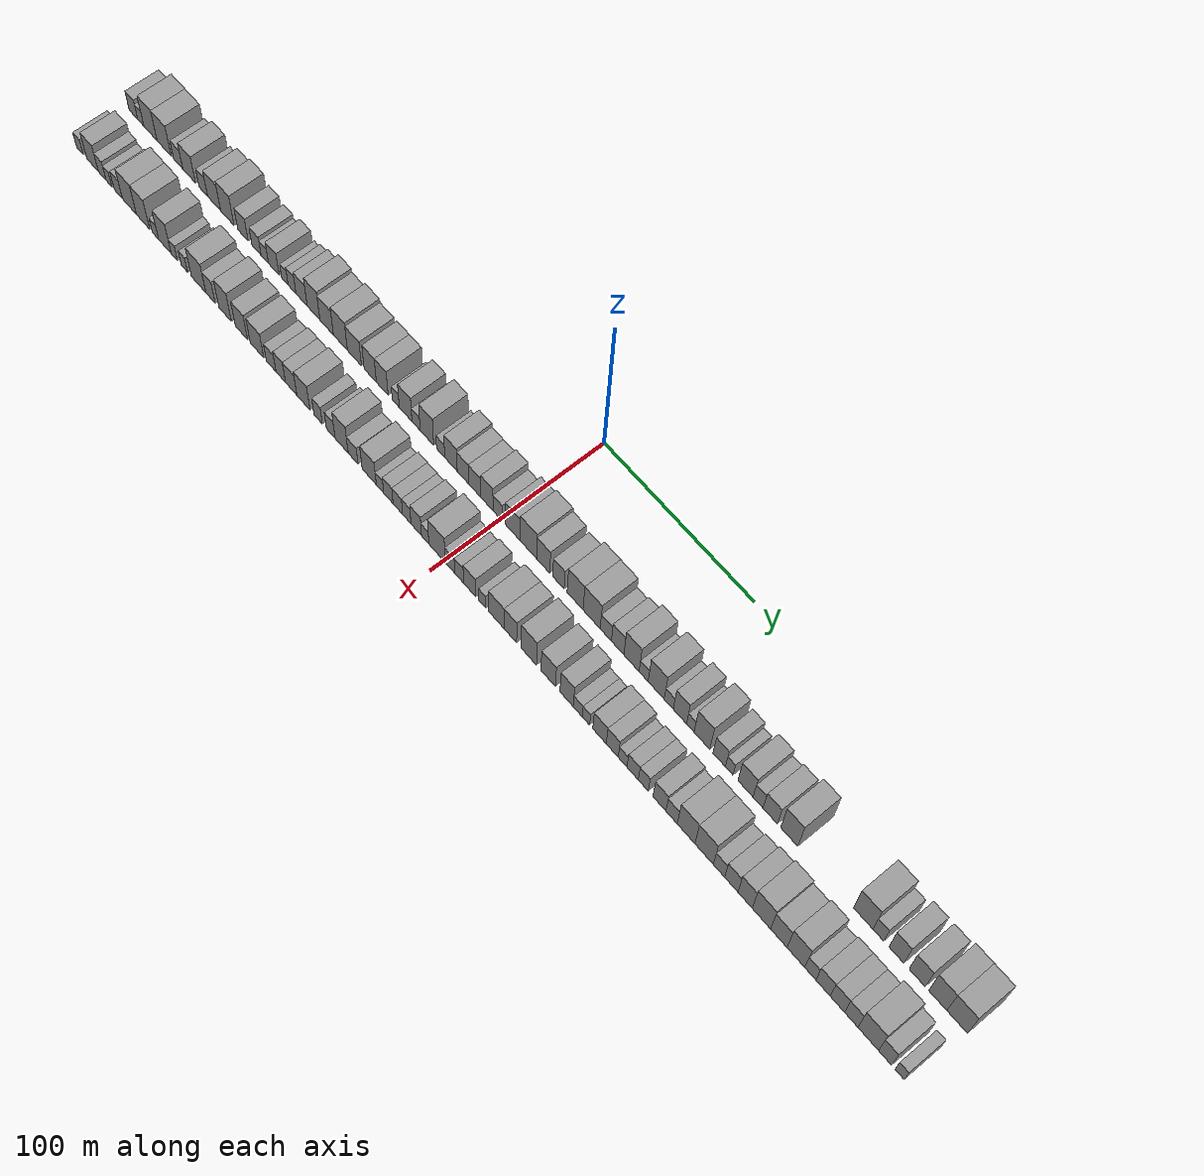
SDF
<sdf version="1.6">
 <world name="default">
  <scene>
   <sky><clouds><speed>12</speed></clouds></sky>
   <ambient>0.4 0.4 0.4 1</ambient>
   <background>0.7 0.7 0.7 1</background>
   <shadows>1</shadows>
  </scene>
  <gravity>0 0 -9.8066</gravity>
  <magnetic_field>6e-06 2.3e-05 -4.2e-05</magnetic_field>
  <physics default="0" name="default_physics" type="ode">
   <ode>
    <solver>
     <type>quick</type>
     <iters>10</iters>
     <sor>1.0</sor>
     <use_dynamic_moi_rescaling>0</use_dynamic_moi_rescaling>
    </solver>
    <constraints>
     <cfm>0</cfm>
     <erp>0.2</erp>
     <contact_max_correcting_vel>100</contact_max_correcting_vel>
     <contact_surface_layer>0.001</contact_surface_layer>
    </constraints>
   </ode>
   <max_step_size>0.004</max_step_size>
   <real_time_factor>1</real_time_factor>
   <real_time_update_rate>250</real_time_update_rate>
  </physics>
  <light name="sun" type="directional">
   <pose>0 0 10 0 0 0</pose>
   <diffuse>0.8 0.8 0.8 1</diffuse>
   <specular>0.2 0.2 0.2 1</specular>
   <attenuation>
    <range>1000</range>
    <constant>0.9</constant>
    <linear>0.01</linear>
    <quadratic>0.001</quadratic>
   </attenuation>
   <direction>-0.5 0.1 -0.9</direction>
  </light>
  <model name="building_1">
   <static>1</static>
   <pose>50.0000 -280.4300 0 0.000000 0.000000 0.000000</pose>
   <link name="link">
    <pose>0 0 7.50 0 0 0</pose>
    <collision name="collision"><geometry><box><size>20.0000 7.1401 15.0000</size></box></geometry></collision>
    <visual name="visual">
     <cast_shadows>0</cast_shadows>
     <geometry><box><size>20.0000 7.1401 15.0000</size></box></geometry>
     <material>
      <script>
       <uri>model://grey_wall/materials/scripts</uri>
       <uri>model://grey_wall/materials/textures</uri>
       <name>vrc/grey_wall</name>
      </script>
     </material>
    </visual>
   </link>
  </model>
  <model name="building_2">
   <static>1</static>
   <pose>50.0000 -274.3220 0 0.000000 0.000000 0.000000</pose>
   <link name="link">
    <pose>0 0 6.00 0 0 0</pose>
    <collision name="collision"><geometry><box><size>20.0000 5.0758 12.0000</size></box></geometry></collision>
    <visual name="visual">
     <cast_shadows>0</cast_shadows>
     <geometry><box><size>20.0000 5.0758 12.0000</size></box></geometry>
     <material>
      <script>
       <uri>model://grey_wall/materials/scripts</uri>
       <uri>model://grey_wall/materials/textures</uri>
       <name>vrc/grey_wall</name>
      </script>
     </material>
    </visual>
   </link>
  </model>
  <model name="building_3">
   <static>1</static>
   <pose>50.0000 -266.2725 0 0.000000 0.000000 0.000000</pose>
   <link name="link">
    <pose>0 0 12.00 0 0 0</pose>
    <collision name="collision"><geometry><box><size>20.0000 11.0232 24.0000</size></box></geometry></collision>
    <visual name="visual">
     <cast_shadows>0</cast_shadows>
     <geometry><box><size>20.0000 11.0232 24.0000</size></box></geometry>
     <material>
      <script>
       <uri>model://grey_wall/materials/scripts</uri>
       <uri>model://grey_wall/materials/textures</uri>
       <name>vrc/grey_wall</name>
      </script>
     </material>
    </visual>
   </link>
  </model>
  <model name="building_4">
   <static>1</static>
   <pose>50.0000 -254.9526 0 0.000000 0.000000 0.000000</pose>
   <link name="link">
    <pose>0 0 12.00 0 0 0</pose>
    <collision name="collision"><geometry><box><size>20.0000 11.6165 24.0000</size></box></geometry></collision>
    <visual name="visual">
     <cast_shadows>0</cast_shadows>
     <geometry><box><size>20.0000 11.6165 24.0000</size></box></geometry>
     <material>
      <script>
       <uri>model://grey_wall/materials/scripts</uri>
       <uri>model://grey_wall/materials/textures</uri>
       <name>vrc/grey_wall</name>
      </script>
     </material>
    </visual>
   </link>
  </model>
  <model name="building_5">
   <static>1</static>
   <pose>50.0000 -243.4171 0 0.000000 0.000000 0.000000</pose>
   <link name="link">
    <pose>0 0 7.50 0 0 0</pose>
    <collision name="collision"><geometry><box><size>20.0000 7.4547 15.0000</size></box></geometry></collision>
    <visual name="visual">
     <cast_shadows>0</cast_shadows>
     <geometry><box><size>20.0000 7.4547 15.0000</size></box></geometry>
     <material>
      <script>
       <uri>model://grey_wall/materials/scripts</uri>
       <uri>model://grey_wall/materials/textures</uri>
       <name>vrc/grey_wall</name>
      </script>
     </material>
    </visual>
   </link>
  </model>
  <model name="building_6">
   <static>1</static>
   <pose>50.0000 -234.5609 0 0.000000 0.000000 0.000000</pose>
   <link name="link">
    <pose>0 0 10.50 0 0 0</pose>
    <collision name="collision"><geometry><box><size>20.0000 10.2577 21.0000</size></box></geometry></collision>
    <visual name="visual">
     <cast_shadows>0</cast_shadows>
     <geometry><box><size>20.0000 10.2577 21.0000</size></box></geometry>
     <material>
      <script>
       <uri>model://grey_wall/materials/scripts</uri>
       <uri>model://grey_wall/materials/textures</uri>
       <name>vrc/grey_wall</name>
      </script>
     </material>
    </visual>
   </link>
  </model>
  <model name="building_7">
   <static>1</static>
   <pose>50.0000 -223.0473 0 0.000000 0.000000 0.000000</pose>
   <link name="link">
    <pose>0 0 7.50 0 0 0</pose>
    <collision name="collision"><geometry><box><size>20.0000 6.7694 15.0000</size></box></geometry></collision>
    <visual name="visual">
     <cast_shadows>0</cast_shadows>
     <geometry><box><size>20.0000 6.7694 15.0000</size></box></geometry>
     <material>
      <script>
       <uri>model://grey_wall/materials/scripts</uri>
       <uri>model://grey_wall/materials/textures</uri>
       <name>vrc/grey_wall</name>
      </script>
     </material>
    </visual>
   </link>
  </model>
  <model name="building_8">
   <static>1</static>
   <pose>50.0000 -214.4296 0 0.000000 0.000000 0.000000</pose>
   <link name="link">
    <pose>0 0 10.50 0 0 0</pose>
    <collision name="collision"><geometry><box><size>20.0000 10.4660 21.0000</size></box></geometry></collision>
    <visual name="visual">
     <cast_shadows>0</cast_shadows>
     <geometry><box><size>20.0000 10.4660 21.0000</size></box></geometry>
     <material>
      <script>
       <uri>model://grey_wall/materials/scripts</uri>
       <uri>model://grey_wall/materials/textures</uri>
       <name>vrc/grey_wall</name>
      </script>
     </material>
    </visual>
   </link>
  </model>
  <model name="building_9">
   <static>1</static>
   <pose>50.0000 -203.8691 0 0.000000 0.000000 0.000000</pose>
   <link name="link">
    <pose>0 0 12.00 0 0 0</pose>
    <collision name="collision"><geometry><box><size>20.0000 10.6550 24.0000</size></box></geometry></collision>
    <visual name="visual">
     <cast_shadows>0</cast_shadows>
     <geometry><box><size>20.0000 10.6550 24.0000</size></box></geometry>
     <material>
      <script>
       <uri>model://grey_wall/materials/scripts</uri>
       <uri>model://grey_wall/materials/textures</uri>
       <name>vrc/grey_wall</name>
      </script>
     </material>
    </visual>
   </link>
  </model>
  <model name="building_10">
   <static>1</static>
   <pose>50.0000 -191.4496 0 0.000000 0.000000 0.000000</pose>
   <link name="link">
    <pose>0 0 9.00 0 0 0</pose>
    <collision name="collision"><geometry><box><size>20.0000 8.1842 18.0000</size></box></geometry></collision>
    <visual name="visual">
     <cast_shadows>0</cast_shadows>
     <geometry><box><size>20.0000 8.1842 18.0000</size></box></geometry>
     <material>
      <script>
       <uri>model://grey_wall/materials/scripts</uri>
       <uri>model://grey_wall/materials/textures</uri>
       <name>vrc/grey_wall</name>
      </script>
     </material>
    </visual>
   </link>
  </model>
  <model name="building_11">
   <static>1</static>
   <pose>50.0000 -180.8008 0 0.000000 0.000000 0.000000</pose>
   <link name="link">
    <pose>0 0 7.50 0 0 0</pose>
    <collision name="collision"><geometry><box><size>20.0000 7.1133 15.0000</size></box></geometry></collision>
    <visual name="visual">
     <cast_shadows>0</cast_shadows>
     <geometry><box><size>20.0000 7.1133 15.0000</size></box></geometry>
     <material>
      <script>
       <uri>model://grey_wall/materials/scripts</uri>
       <uri>model://grey_wall/materials/textures</uri>
       <name>vrc/grey_wall</name>
      </script>
     </material>
    </visual>
   </link>
  </model>
  <model name="building_12">
   <static>1</static>
   <pose>50.0000 -174.3327 0 0.000000 0.000000 0.000000</pose>
   <link name="link">
    <pose>0 0 6.00 0 0 0</pose>
    <collision name="collision"><geometry><box><size>20.0000 5.8230 12.0000</size></box></geometry></collision>
    <visual name="visual">
     <cast_shadows>0</cast_shadows>
     <geometry><box><size>20.0000 5.8230 12.0000</size></box></geometry>
     <material>
      <script>
       <uri>model://grey_wall/materials/scripts</uri>
       <uri>model://grey_wall/materials/textures</uri>
       <name>vrc/grey_wall</name>
      </script>
     </material>
    </visual>
   </link>
  </model>
  <model name="building_13">
   <static>1</static>
   <pose>50.0000 -167.2773 0 0.000000 0.000000 0.000000</pose>
   <link name="link">
    <pose>0 0 9.00 0 0 0</pose>
    <collision name="collision"><geometry><box><size>20.0000 8.2878 18.0000</size></box></geometry></collision>
    <visual name="visual">
     <cast_shadows>0</cast_shadows>
     <geometry><box><size>20.0000 8.2878 18.0000</size></box></geometry>
     <material>
      <script>
       <uri>model://grey_wall/materials/scripts</uri>
       <uri>model://grey_wall/materials/textures</uri>
       <name>vrc/grey_wall</name>
      </script>
     </material>
    </visual>
   </link>
  </model>
  <model name="building_14">
   <static>1</static>
   <pose>50.0000 -158.6507 0 0.000000 0.000000 0.000000</pose>
   <link name="link">
    <pose>0 0 6.00 0 0 0</pose>
    <collision name="collision"><geometry><box><size>20.0000 4.9654 12.0000</size></box></geometry></collision>
    <visual name="visual">
     <cast_shadows>0</cast_shadows>
     <geometry><box><size>20.0000 4.9654 12.0000</size></box></geometry>
     <material>
      <script>
       <uri>model://grey_wall/materials/scripts</uri>
       <uri>model://grey_wall/materials/textures</uri>
       <name>vrc/grey_wall</name>
      </script>
     </material>
    </visual>
   </link>
  </model>
  <model name="building_15">
   <static>1</static>
   <pose>50.0000 -153.1409 0 0.000000 0.000000 0.000000</pose>
   <link name="link">
    <pose>0 0 7.50 0 0 0</pose>
    <collision name="collision"><geometry><box><size>20.0000 6.0542 15.0000</size></box></geometry></collision>
    <visual name="visual">
     <cast_shadows>0</cast_shadows>
     <geometry><box><size>20.0000 6.0542 15.0000</size></box></geometry>
     <material>
      <script>
       <uri>model://grey_wall/materials/scripts</uri>
       <uri>model://grey_wall/materials/textures</uri>
       <name>vrc/grey_wall</name>
      </script>
     </material>
    </visual>
   </link>
  </model>
  <model name="building_16">
   <static>1</static>
   <pose>50.0000 -145.7998 0 0.000000 0.000000 0.000000</pose>
   <link name="link">
    <pose>0 0 9.00 0 0 0</pose>
    <collision name="collision"><geometry><box><size>20.0000 8.6280 18.0000</size></box></geometry></collision>
    <visual name="visual">
     <cast_shadows>0</cast_shadows>
     <geometry><box><size>20.0000 8.6280 18.0000</size></box></geometry>
     <material>
      <script>
       <uri>model://grey_wall/materials/scripts</uri>
       <uri>model://grey_wall/materials/textures</uri>
       <name>vrc/grey_wall</name>
      </script>
     </material>
    </visual>
   </link>
  </model>
  <model name="building_17">
   <static>1</static>
   <pose>50.0000 -136.6325 0 0.000000 0.000000 0.000000</pose>
   <link name="link">
    <pose>0 0 12.00 0 0 0</pose>
    <collision name="collision"><geometry><box><size>20.0000 9.7068 24.0000</size></box></geometry></collision>
    <visual name="visual">
     <cast_shadows>0</cast_shadows>
     <geometry><box><size>20.0000 9.7068 24.0000</size></box></geometry>
     <material>
      <script>
       <uri>model://grey_wall/materials/scripts</uri>
       <uri>model://grey_wall/materials/textures</uri>
       <name>vrc/grey_wall</name>
      </script>
     </material>
    </visual>
   </link>
  </model>
  <model name="building_18">
   <static>1</static>
   <pose>50.0000 -126.6958 0 0.000000 0.000000 0.000000</pose>
   <link name="link">
    <pose>0 0 10.50 0 0 0</pose>
    <collision name="collision"><geometry><box><size>20.0000 10.1666 21.0000</size></box></geometry></collision>
    <visual name="visual">
     <cast_shadows>0</cast_shadows>
     <geometry><box><size>20.0000 10.1666 21.0000</size></box></geometry>
     <material>
      <script>
       <uri>model://grey_wall/materials/scripts</uri>
       <uri>model://grey_wall/materials/textures</uri>
       <name>vrc/grey_wall</name>
      </script>
     </material>
    </visual>
   </link>
  </model>
  <model name="building_19">
   <static>1</static>
   <pose>50.0000 -116.3341 0 0.000000 0.000000 0.000000</pose>
   <link name="link">
    <pose>0 0 12.00 0 0 0</pose>
    <collision name="collision"><geometry><box><size>20.0000 10.5568 24.0000</size></box></geometry></collision>
    <visual name="visual">
     <cast_shadows>0</cast_shadows>
     <geometry><box><size>20.0000 10.5568 24.0000</size></box></geometry>
     <material>
      <script>
       <uri>model://grey_wall/materials/scripts</uri>
       <uri>model://grey_wall/materials/textures</uri>
       <name>vrc/grey_wall</name>
      </script>
     </material>
    </visual>
   </link>
  </model>
  <model name="building_20">
   <static>1</static>
   <pose>50.0000 -105.8217 0 0.000000 0.000000 0.000000</pose>
   <link name="link">
    <pose>0 0 10.50 0 0 0</pose>
    <collision name="collision"><geometry><box><size>20.0000 10.4680 21.0000</size></box></geometry></collision>
    <visual name="visual">
     <cast_shadows>0</cast_shadows>
     <geometry><box><size>20.0000 10.4680 21.0000</size></box></geometry>
     <material>
      <script>
       <uri>model://grey_wall/materials/scripts</uri>
       <uri>model://grey_wall/materials/textures</uri>
       <name>vrc/grey_wall</name>
      </script>
     </material>
    </visual>
   </link>
  </model>
  <model name="building_21">
   <static>1</static>
   <pose>50.0000 -94.0558 0 0.000000 0.000000 0.000000</pose>
   <link name="link">
    <pose>0 0 10.50 0 0 0</pose>
    <collision name="collision"><geometry><box><size>20.0000 9.0638 21.0000</size></box></geometry></collision>
    <visual name="visual">
     <cast_shadows>0</cast_shadows>
     <geometry><box><size>20.0000 9.0638 21.0000</size></box></geometry>
     <material>
      <script>
       <uri>model://grey_wall/materials/scripts</uri>
       <uri>model://grey_wall/materials/textures</uri>
       <name>vrc/grey_wall</name>
      </script>
     </material>
    </visual>
   </link>
  </model>
  <model name="building_22">
   <static>1</static>
   <pose>50.0000 -85.1823 0 0.000000 0.000000 0.000000</pose>
   <link name="link">
    <pose>0 0 10.50 0 0 0</pose>
    <collision name="collision"><geometry><box><size>20.0000 8.6832 21.0000</size></box></geometry></collision>
    <visual name="visual">
     <cast_shadows>0</cast_shadows>
     <geometry><box><size>20.0000 8.6832 21.0000</size></box></geometry>
     <material>
      <script>
       <uri>model://grey_wall/materials/scripts</uri>
       <uri>model://grey_wall/materials/textures</uri>
       <name>vrc/grey_wall</name>
      </script>
     </material>
    </visual>
   </link>
  </model>
  <model name="building_23">
   <static>1</static>
   <pose>50.0000 -75.2520 0 0.000000 0.000000 0.000000</pose>
   <link name="link">
    <pose>0 0 6.00 0 0 0</pose>
    <collision name="collision"><geometry><box><size>20.0000 5.1775 12.0000</size></box></geometry></collision>
    <visual name="visual">
     <cast_shadows>0</cast_shadows>
     <geometry><box><size>20.0000 5.1775 12.0000</size></box></geometry>
     <material>
      <script>
       <uri>model://grey_wall/materials/scripts</uri>
       <uri>model://grey_wall/materials/textures</uri>
       <name>vrc/grey_wall</name>
      </script>
     </material>
    </visual>
   </link>
  </model>
  <model name="building_24">
   <static>1</static>
   <pose>50.0000 -68.0340 0 0.000000 0.000000 0.000000</pose>
   <link name="link">
    <pose>0 0 10.50 0 0 0</pose>
    <collision name="collision"><geometry><box><size>20.0000 9.2584 21.0000</size></box></geometry></collision>
    <visual name="visual">
     <cast_shadows>0</cast_shadows>
     <geometry><box><size>20.0000 9.2584 21.0000</size></box></geometry>
     <material>
      <script>
       <uri>model://grey_wall/materials/scripts</uri>
       <uri>model://grey_wall/materials/textures</uri>
       <name>vrc/grey_wall</name>
      </script>
     </material>
    </visual>
   </link>
  </model>
  <model name="building_25">
   <static>1</static>
   <pose>50.0000 -60.4463 0 0.000000 0.000000 0.000000</pose>
   <link name="link">
    <pose>0 0 6.00 0 0 0</pose>
    <collision name="collision"><geometry><box><size>20.0000 5.9170 12.0000</size></box></geometry></collision>
    <visual name="visual">
     <cast_shadows>0</cast_shadows>
     <geometry><box><size>20.0000 5.9170 12.0000</size></box></geometry>
     <material>
      <script>
       <uri>model://grey_wall/materials/scripts</uri>
       <uri>model://grey_wall/materials/textures</uri>
       <name>vrc/grey_wall</name>
      </script>
     </material>
    </visual>
   </link>
  </model>
  <model name="building_26">
   <static>1</static>
   <pose>50.0000 -52.6109 0 0.000000 0.000000 0.000000</pose>
   <link name="link">
    <pose>0 0 12.00 0 0 0</pose>
    <collision name="collision"><geometry><box><size>20.0000 9.7540 24.0000</size></box></geometry></collision>
    <visual name="visual">
     <cast_shadows>0</cast_shadows>
     <geometry><box><size>20.0000 9.7540 24.0000</size></box></geometry>
     <material>
      <script>
       <uri>model://grey_wall/materials/scripts</uri>
       <uri>model://grey_wall/materials/textures</uri>
       <name>vrc/grey_wall</name>
      </script>
     </material>
    </visual>
   </link>
  </model>
  <model name="building_27">
   <static>1</static>
   <pose>50.0000 -42.7771 0 0.000000 0.000000 0.000000</pose>
   <link name="link">
    <pose>0 0 6.00 0 0 0</pose>
    <collision name="collision"><geometry><box><size>20.0000 5.9135 12.0000</size></box></geometry></collision>
    <visual name="visual">
     <cast_shadows>0</cast_shadows>
     <geometry><box><size>20.0000 5.9135 12.0000</size></box></geometry>
     <material>
      <script>
       <uri>model://grey_wall/materials/scripts</uri>
       <uri>model://grey_wall/materials/textures</uri>
       <name>vrc/grey_wall</name>
      </script>
     </material>
    </visual>
   </link>
  </model>
  <model name="building_28">
   <static>1</static>
   <pose>50.0000 -35.3607 0 0.000000 0.000000 0.000000</pose>
   <link name="link">
    <pose>0 0 10.50 0 0 0</pose>
    <collision name="collision"><geometry><box><size>20.0000 8.9193 21.0000</size></box></geometry></collision>
    <visual name="visual">
     <cast_shadows>0</cast_shadows>
     <geometry><box><size>20.0000 8.9193 21.0000</size></box></geometry>
     <material>
      <script>
       <uri>model://grey_wall/materials/scripts</uri>
       <uri>model://grey_wall/materials/textures</uri>
       <name>vrc/grey_wall</name>
      </script>
     </material>
    </visual>
   </link>
  </model>
  <model name="building_29">
   <static>1</static>
   <pose>50.0000 -26.9006 0 0.000000 0.000000 0.000000</pose>
   <link name="link">
    <pose>0 0 9.00 0 0 0</pose>
    <collision name="collision"><geometry><box><size>20.0000 8.0008 18.0000</size></box></geometry></collision>
    <visual name="visual">
     <cast_shadows>0</cast_shadows>
     <geometry><box><size>20.0000 8.0008 18.0000</size></box></geometry>
     <material>
      <script>
       <uri>model://grey_wall/materials/scripts</uri>
       <uri>model://grey_wall/materials/textures</uri>
       <name>vrc/grey_wall</name>
      </script>
     </material>
    </visual>
   </link>
  </model>
  <model name="building_30">
   <static>1</static>
   <pose>50.0000 -18.5486 0 0.000000 0.000000 0.000000</pose>
   <link name="link">
    <pose>0 0 9.00 0 0 0</pose>
    <collision name="collision"><geometry><box><size>20.0000 8.7033 18.0000</size></box></geometry></collision>
    <visual name="visual">
     <cast_shadows>0</cast_shadows>
     <geometry><box><size>20.0000 8.7033 18.0000</size></box></geometry>
     <material>
      <script>
       <uri>model://grey_wall/materials/scripts</uri>
       <uri>model://grey_wall/materials/textures</uri>
       <name>vrc/grey_wall</name>
      </script>
     </material>
    </visual>
   </link>
  </model>
  <model name="building_31">
   <static>1</static>
   <pose>50.0000 -9.9834 0 0.000000 0.000000 0.000000</pose>
   <link name="link">
    <pose>0 0 10.50 0 0 0</pose>
    <collision name="collision"><geometry><box><size>20.0000 8.4271 21.0000</size></box></geometry></collision>
    <visual name="visual">
     <cast_shadows>0</cast_shadows>
     <geometry><box><size>20.0000 8.4271 21.0000</size></box></geometry>
     <material>
      <script>
       <uri>model://grey_wall/materials/scripts</uri>
       <uri>model://grey_wall/materials/textures</uri>
       <name>vrc/grey_wall</name>
      </script>
     </material>
    </visual>
   </link>
  </model>
  <model name="building_32">
   <static>1</static>
   <pose>50.0000 -2.4643 0 0.000000 0.000000 0.000000</pose>
   <link name="link">
    <pose>0 0 7.50 0 0 0</pose>
    <collision name="collision"><geometry><box><size>20.0000 6.6110 15.0000</size></box></geometry></collision>
    <visual name="visual">
     <cast_shadows>0</cast_shadows>
     <geometry><box><size>20.0000 6.6110 15.0000</size></box></geometry>
     <material>
      <script>
       <uri>model://grey_wall/materials/scripts</uri>
       <uri>model://grey_wall/materials/textures</uri>
       <name>vrc/grey_wall</name>
      </script>
     </material>
    </visual>
   </link>
  </model>
  <model name="building_33">
   <static>1</static>
   <pose>50.0000 7.9757 0 0.000000 0.000000 0.000000</pose>
   <link name="link">
    <pose>0 0 10.50 0 0 0</pose>
    <collision name="collision"><geometry><box><size>20.0000 10.2690 21.0000</size></box></geometry></collision>
    <visual name="visual">
     <cast_shadows>0</cast_shadows>
     <geometry><box><size>20.0000 10.2690 21.0000</size></box></geometry>
     <material>
      <script>
       <uri>model://grey_wall/materials/scripts</uri>
       <uri>model://grey_wall/materials/textures</uri>
       <name>vrc/grey_wall</name>
      </script>
     </material>
    </visual>
   </link>
  </model>
  <model name="building_34">
   <static>1</static>
   <pose>50.0000 18.7712 0 0.000000 0.000000 0.000000</pose>
   <link name="link">
    <pose>0 0 12.00 0 0 0</pose>
    <collision name="collision"><geometry><box><size>20.0000 11.3220 24.0000</size></box></geometry></collision>
    <visual name="visual">
     <cast_shadows>0</cast_shadows>
     <geometry><box><size>20.0000 11.3220 24.0000</size></box></geometry>
     <material>
      <script>
       <uri>model://grey_wall/materials/scripts</uri>
       <uri>model://grey_wall/materials/textures</uri>
       <name>vrc/grey_wall</name>
      </script>
     </material>
    </visual>
   </link>
  </model>
  <model name="building_35">
   <static>1</static>
   <pose>50.0000 28.8956 0 0.000000 0.000000 0.000000</pose>
   <link name="link">
    <pose>0 0 10.50 0 0 0</pose>
    <collision name="collision"><geometry><box><size>20.0000 8.9268 21.0000</size></box></geometry></collision>
    <visual name="visual">
     <cast_shadows>0</cast_shadows>
     <geometry><box><size>20.0000 8.9268 21.0000</size></box></geometry>
     <material>
      <script>
       <uri>model://grey_wall/materials/scripts</uri>
       <uri>model://grey_wall/materials/textures</uri>
       <name>vrc/grey_wall</name>
      </script>
     </material>
    </visual>
   </link>
  </model>
  <model name="building_36">
   <static>1</static>
   <pose>50.0000 39.2411 0 0.000000 0.000000 0.000000</pose>
   <link name="link">
    <pose>0 0 9.00 0 0 0</pose>
    <collision name="collision"><geometry><box><size>20.0000 7.7642 18.0000</size></box></geometry></collision>
    <visual name="visual">
     <cast_shadows>0</cast_shadows>
     <geometry><box><size>20.0000 7.7642 18.0000</size></box></geometry>
     <material>
      <script>
       <uri>model://grey_wall/materials/scripts</uri>
       <uri>model://grey_wall/materials/textures</uri>
       <name>vrc/grey_wall</name>
      </script>
     </material>
    </visual>
   </link>
  </model>
  <model name="building_37">
   <static>1</static>
   <pose>50.0000 50.4694 0 0.000000 0.000000 0.000000</pose>
   <link name="link">
    <pose>0 0 12.00 0 0 0</pose>
    <collision name="collision"><geometry><box><size>20.0000 10.6924 24.0000</size></box></geometry></collision>
    <visual name="visual">
     <cast_shadows>0</cast_shadows>
     <geometry><box><size>20.0000 10.6924 24.0000</size></box></geometry>
     <material>
      <script>
       <uri>model://grey_wall/materials/scripts</uri>
       <uri>model://grey_wall/materials/textures</uri>
       <name>vrc/grey_wall</name>
      </script>
     </material>
    </visual>
   </link>
  </model>
  <model name="building_38">
   <static>1</static>
   <pose>50.0000 61.5156 0 0.000000 0.000000 0.000000</pose>
   <link name="link">
    <pose>0 0 12.00 0 0 0</pose>
    <collision name="collision"><geometry><box><size>20.0000 11.3999 24.0000</size></box></geometry></collision>
    <visual name="visual">
     <cast_shadows>0</cast_shadows>
     <geometry><box><size>20.0000 11.3999 24.0000</size></box></geometry>
     <material>
      <script>
       <uri>model://grey_wall/materials/scripts</uri>
       <uri>model://grey_wall/materials/textures</uri>
       <name>vrc/grey_wall</name>
      </script>
     </material>
    </visual>
   </link>
  </model>
  <model name="building_39">
   <static>1</static>
   <pose>50.0000 70.9410 0 0.000000 0.000000 0.000000</pose>
   <link name="link">
    <pose>0 0 7.50 0 0 0</pose>
    <collision name="collision"><geometry><box><size>20.0000 7.4509 15.0000</size></box></geometry></collision>
    <visual name="visual">
     <cast_shadows>0</cast_shadows>
     <geometry><box><size>20.0000 7.4509 15.0000</size></box></geometry>
     <material>
      <script>
       <uri>model://grey_wall/materials/scripts</uri>
       <uri>model://grey_wall/materials/textures</uri>
       <name>vrc/grey_wall</name>
      </script>
     </material>
    </visual>
   </link>
  </model>
  <model name="building_40">
   <static>1</static>
   <pose>50.0000 78.7618 0 0.000000 0.000000 0.000000</pose>
   <link name="link">
    <pose>0 0 9.00 0 0 0</pose>
    <collision name="collision"><geometry><box><size>20.0000 8.1908 18.0000</size></box></geometry></collision>
    <visual name="visual">
     <cast_shadows>0</cast_shadows>
     <geometry><box><size>20.0000 8.1908 18.0000</size></box></geometry>
     <material>
      <script>
       <uri>model://grey_wall/materials/scripts</uri>
       <uri>model://grey_wall/materials/textures</uri>
       <name>vrc/grey_wall</name>
      </script>
     </material>
    </visual>
   </link>
  </model>
  <model name="building_41">
   <static>1</static>
   <pose>50.0000 87.8269 0 0.000000 0.000000 0.000000</pose>
   <link name="link">
    <pose>0 0 12.00 0 0 0</pose>
    <collision name="collision"><geometry><box><size>20.0000 9.9394 24.0000</size></box></geometry></collision>
    <visual name="visual">
     <cast_shadows>0</cast_shadows>
     <geometry><box><size>20.0000 9.9394 24.0000</size></box></geometry>
     <material>
      <script>
       <uri>model://grey_wall/materials/scripts</uri>
       <uri>model://grey_wall/materials/textures</uri>
       <name>vrc/grey_wall</name>
      </script>
     </material>
    </visual>
   </link>
  </model>
  <model name="building_42">
   <static>1</static>
   <pose>50.0000 95.7598 0 0.000000 0.000000 0.000000</pose>
   <link name="link">
    <pose>0 0 6.00 0 0 0</pose>
    <collision name="collision"><geometry><box><size>20.0000 5.9263 12.0000</size></box></geometry></collision>
    <visual name="visual">
     <cast_shadows>0</cast_shadows>
     <geometry><box><size>20.0000 5.9263 12.0000</size></box></geometry>
     <material>
      <script>
       <uri>model://grey_wall/materials/scripts</uri>
       <uri>model://grey_wall/materials/textures</uri>
       <name>vrc/grey_wall</name>
      </script>
     </material>
    </visual>
   </link>
  </model>
  <model name="building_43">
   <static>1</static>
   <pose>50.0000 103.9115 0 0.000000 0.000000 0.000000</pose>
   <link name="link">
    <pose>0 0 12.00 0 0 0</pose>
    <collision name="collision"><geometry><box><size>20.0000 10.3771 24.0000</size></box></geometry></collision>
    <visual name="visual">
     <cast_shadows>0</cast_shadows>
     <geometry><box><size>20.0000 10.3771 24.0000</size></box></geometry>
     <material>
      <script>
       <uri>model://grey_wall/materials/scripts</uri>
       <uri>model://grey_wall/materials/textures</uri>
       <name>vrc/grey_wall</name>
      </script>
     </material>
    </visual>
   </link>
  </model>
  <model name="building_44">
   <static>1</static>
   <pose>50.0000 112.0410 0 0.000000 0.000000 0.000000</pose>
   <link name="link">
    <pose>0 0 6.00 0 0 0</pose>
    <collision name="collision"><geometry><box><size>20.0000 5.8819 12.0000</size></box></geometry></collision>
    <visual name="visual">
     <cast_shadows>0</cast_shadows>
     <geometry><box><size>20.0000 5.8819 12.0000</size></box></geometry>
     <material>
      <script>
       <uri>model://grey_wall/materials/scripts</uri>
       <uri>model://grey_wall/materials/textures</uri>
       <name>vrc/grey_wall</name>
      </script>
     </material>
    </visual>
   </link>
  </model>
  <model name="building_45">
   <static>1</static>
   <pose>50.0000 119.2341 0 0.000000 0.000000 0.000000</pose>
   <link name="link">
    <pose>0 0 10.50 0 0 0</pose>
    <collision name="collision"><geometry><box><size>20.0000 8.5043 21.0000</size></box></geometry></collision>
    <visual name="visual">
     <cast_shadows>0</cast_shadows>
     <geometry><box><size>20.0000 8.5043 21.0000</size></box></geometry>
     <material>
      <script>
       <uri>model://grey_wall/materials/scripts</uri>
       <uri>model://grey_wall/materials/textures</uri>
       <name>vrc/grey_wall</name>
      </script>
     </material>
    </visual>
   </link>
  </model>
  <model name="building_46">
   <static>1</static>
   <pose>50.0000 125.8914 0 0.000000 0.000000 0.000000</pose>
   <link name="link">
    <pose>0 0 6.00 0 0 0</pose>
    <collision name="collision"><geometry><box><size>20.0000 4.8104 12.0000</size></box></geometry></collision>
    <visual name="visual">
     <cast_shadows>0</cast_shadows>
     <geometry><box><size>20.0000 4.8104 12.0000</size></box></geometry>
     <material>
      <script>
       <uri>model://grey_wall/materials/scripts</uri>
       <uri>model://grey_wall/materials/textures</uri>
       <name>vrc/grey_wall</name>
      </script>
     </material>
    </visual>
   </link>
  </model>
  <model name="building_47">
   <static>1</static>
   <pose>50.0000 133.2575 0 0.000000 0.000000 0.000000</pose>
   <link name="link">
    <pose>0 0 12.00 0 0 0</pose>
    <collision name="collision"><geometry><box><size>20.0000 9.9218 24.0000</size></box></geometry></collision>
    <visual name="visual">
     <cast_shadows>0</cast_shadows>
     <geometry><box><size>20.0000 9.9218 24.0000</size></box></geometry>
     <material>
      <script>
       <uri>model://grey_wall/materials/scripts</uri>
       <uri>model://grey_wall/materials/textures</uri>
       <name>vrc/grey_wall</name>
      </script>
     </material>
    </visual>
   </link>
  </model>
  <model name="building_48">
   <static>1</static>
   <pose>50.0000 144.1445 0 0.000000 0.000000 0.000000</pose>
   <link name="link">
    <pose>0 0 9.00 0 0 0</pose>
    <collision name="collision"><geometry><box><size>20.0000 7.8521 18.0000</size></box></geometry></collision>
    <visual name="visual">
     <cast_shadows>0</cast_shadows>
     <geometry><box><size>20.0000 7.8521 18.0000</size></box></geometry>
     <material>
      <script>
       <uri>model://grey_wall/materials/scripts</uri>
       <uri>model://grey_wall/materials/textures</uri>
       <name>vrc/grey_wall</name>
      </script>
     </material>
    </visual>
   </link>
  </model>
  <model name="building_49">
   <static>1</static>
   <pose>50.0000 150.4758 0 0.000000 0.000000 0.000000</pose>
   <link name="link">
    <pose>0 0 6.00 0 0 0</pose>
    <collision name="collision"><geometry><box><size>20.0000 4.8105 12.0000</size></box></geometry></collision>
    <visual name="visual">
     <cast_shadows>0</cast_shadows>
     <geometry><box><size>20.0000 4.8105 12.0000</size></box></geometry>
     <material>
      <script>
       <uri>model://grey_wall/materials/scripts</uri>
       <uri>model://grey_wall/materials/textures</uri>
       <name>vrc/grey_wall</name>
      </script>
     </material>
    </visual>
   </link>
  </model>
  <model name="building_50">
   <static>1</static>
   <pose>50.0000 160.5811 0 0.000000 0.000000 0.000000</pose>
   <link name="link">
    <pose>0 0 10.50 0 0 0</pose>
    <collision name="collision"><geometry><box><size>20.0000 9.4002 21.0000</size></box></geometry></collision>
    <visual name="visual">
     <cast_shadows>0</cast_shadows>
     <geometry><box><size>20.0000 9.4002 21.0000</size></box></geometry>
     <material>
      <script>
       <uri>model://grey_wall/materials/scripts</uri>
       <uri>model://grey_wall/materials/textures</uri>
       <name>vrc/grey_wall</name>
      </script>
     </material>
    </visual>
   </link>
  </model>
  <model name="building_51">
   <static>1</static>
   <pose>50.0000 168.3770 0 0.000000 0.000000 0.000000</pose>
   <link name="link">
    <pose>0 0 7.50 0 0 0</pose>
    <collision name="collision"><geometry><box><size>20.0000 6.1916 15.0000</size></box></geometry></collision>
    <visual name="visual">
     <cast_shadows>0</cast_shadows>
     <geometry><box><size>20.0000 6.1916 15.0000</size></box></geometry>
     <material>
      <script>
       <uri>model://grey_wall/materials/scripts</uri>
       <uri>model://grey_wall/materials/textures</uri>
       <name>vrc/grey_wall</name>
      </script>
     </material>
    </visual>
   </link>
  </model>
  <model name="building_52">
   <static>1</static>
   <pose>50.0000 175.8885 0 0.000000 0.000000 0.000000</pose>
   <link name="link">
    <pose>0 0 9.00 0 0 0</pose>
    <collision name="collision"><geometry><box><size>20.0000 8.8314 18.0000</size></box></geometry></collision>
    <visual name="visual">
     <cast_shadows>0</cast_shadows>
     <geometry><box><size>20.0000 8.8314 18.0000</size></box></geometry>
     <material>
      <script>
       <uri>model://grey_wall/materials/scripts</uri>
       <uri>model://grey_wall/materials/textures</uri>
       <name>vrc/grey_wall</name>
      </script>
     </material>
    </visual>
   </link>
  </model>
  <model name="building_53">
   <static>1</static>
   <pose>50.0000 187.5169 0 0.000000 0.000000 0.000000</pose>
   <link name="link">
    <pose>0 0 12.00 0 0 0</pose>
    <collision name="collision"><geometry><box><size>20.0000 10.4254 24.0000</size></box></geometry></collision>
    <visual name="visual">
     <cast_shadows>0</cast_shadows>
     <geometry><box><size>20.0000 10.4254 24.0000</size></box></geometry>
     <material>
      <script>
       <uri>model://grey_wall/materials/scripts</uri>
       <uri>model://grey_wall/materials/textures</uri>
       <name>vrc/grey_wall</name>
      </script>
     </material>
    </visual>
   </link>
  </model>
  <model name="building_54">
   <static>1</static>
   <pose>50.0000 231.8937 0 0.000000 0.000000 0.000000</pose>
   <link name="link">
    <pose>0 0 12.00 0 0 0</pose>
    <collision name="collision"><geometry><box><size>20.0000 11.4427 24.0000</size></box></geometry></collision>
    <visual name="visual">
     <cast_shadows>0</cast_shadows>
     <geometry><box><size>20.0000 11.4427 24.0000</size></box></geometry>
     <material>
      <script>
       <uri>model://grey_wall/materials/scripts</uri>
       <uri>model://grey_wall/materials/textures</uri>
       <name>vrc/grey_wall</name>
      </script>
     </material>
    </visual>
   </link>
  </model>
  <model name="building_55">
   <static>1</static>
   <pose>50.0000 240.7712 0 0.000000 0.000000 0.000000</pose>
   <link name="link">
    <pose>0 0 7.50 0 0 0</pose>
    <collision name="collision"><geometry><box><size>20.0000 6.3123 15.0000</size></box></geometry></collision>
    <visual name="visual">
     <cast_shadows>0</cast_shadows>
     <geometry><box><size>20.0000 6.3123 15.0000</size></box></geometry>
     <material>
      <script>
       <uri>model://grey_wall/materials/scripts</uri>
       <uri>model://grey_wall/materials/textures</uri>
       <name>vrc/grey_wall</name>
      </script>
     </material>
    </visual>
   </link>
  </model>
  <model name="building_56">
   <static>1</static>
   <pose>50.0000 251.2696 0 0.000000 0.000000 0.000000</pose>
   <link name="link">
    <pose>0 0 10.50 0 0 0</pose>
    <collision name="collision"><geometry><box><size>20.0000 8.6844 21.0000</size></box></geometry></collision>
    <visual name="visual">
     <cast_shadows>0</cast_shadows>
     <geometry><box><size>20.0000 8.6844 21.0000</size></box></geometry>
     <material>
      <script>
       <uri>model://grey_wall/materials/scripts</uri>
       <uri>model://grey_wall/materials/textures</uri>
       <name>vrc/grey_wall</name>
      </script>
     </material>
    </visual>
   </link>
  </model>
  <model name="building_57">
   <static>1</static>
   <pose>50.0000 263.2645 0 0.000000 0.000000 0.000000</pose>
   <link name="link">
    <pose>0 0 10.50 0 0 0</pose>
    <collision name="collision"><geometry><box><size>20.0000 9.3053 21.0000</size></box></geometry></collision>
    <visual name="visual">
     <cast_shadows>0</cast_shadows>
     <geometry><box><size>20.0000 9.3053 21.0000</size></box></geometry>
     <material>
      <script>
       <uri>model://grey_wall/materials/scripts</uri>
       <uri>model://grey_wall/materials/textures</uri>
       <name>vrc/grey_wall</name>
      </script>
     </material>
    </visual>
   </link>
  </model>
  <model name="building_58">
   <static>1</static>
   <pose>50.0000 275.0928 0 0.000000 0.000000 0.000000</pose>
   <link name="link">
    <pose>0 0 12.00 0 0 0</pose>
    <collision name="collision"><geometry><box><size>20.0000 10.3512 24.0000</size></box></geometry></collision>
    <visual name="visual">
     <cast_shadows>0</cast_shadows>
     <geometry><box><size>20.0000 10.3512 24.0000</size></box></geometry>
     <material>
      <script>
       <uri>model://grey_wall/materials/scripts</uri>
       <uri>model://grey_wall/materials/textures</uri>
       <name>vrc/grey_wall</name>
      </script>
     </material>
    </visual>
   </link>
  </model>
  <model name="building_59">
   <static>1</static>
   <pose>50.0000 286.1208 0 0.000000 0.000000 0.000000</pose>
   <link name="link">
    <pose>0 0 12.00 0 0 0</pose>
    <collision name="collision"><geometry><box><size>20.0000 11.7048 24.0000</size></box></geometry></collision>
    <visual name="visual">
     <cast_shadows>0</cast_shadows>
     <geometry><box><size>20.0000 11.7048 24.0000</size></box></geometry>
     <material>
      <script>
       <uri>model://grey_wall/materials/scripts</uri>
       <uri>model://grey_wall/materials/textures</uri>
       <name>vrc/grey_wall</name>
      </script>
     </material>
    </visual>
   </link>
  </model>
  <model name="building_60">
   <static>1</static>
   <pose>82.0000 -279.2086 0 0.000000 0.000000 0.000000</pose>
   <link name="link">
    <pose>0 0 6.00 0 0 0</pose>
    <collision name="collision"><geometry><box><size>20.0000 5.5827 12.0000</size></box></geometry></collision>
    <visual name="visual">
     <cast_shadows>0</cast_shadows>
     <geometry><box><size>20.0000 5.5827 12.0000</size></box></geometry>
     <material>
      <script>
       <uri>model://grey_wall/materials/scripts</uri>
       <uri>model://grey_wall/materials/textures</uri>
       <name>vrc/grey_wall</name>
      </script>
     </material>
    </visual>
   </link>
  </model>
  <model name="building_61">
   <static>1</static>
   <pose>82.0000 -268.5561 0 0.000000 0.000000 0.000000</pose>
   <link name="link">
    <pose>0 0 10.50 0 0 0</pose>
    <collision name="collision"><geometry><box><size>20.0000 9.7223 21.0000</size></box></geometry></collision>
    <visual name="visual">
     <cast_shadows>0</cast_shadows>
     <geometry><box><size>20.0000 9.7223 21.0000</size></box></geometry>
     <material>
      <script>
       <uri>model://grey_wall/materials/scripts</uri>
       <uri>model://grey_wall/materials/textures</uri>
       <name>vrc/grey_wall</name>
      </script>
     </material>
    </visual>
   </link>
  </model>
  <model name="building_62">
   <static>1</static>
   <pose>82.0000 -260.5660 0 0.000000 0.000000 0.000000</pose>
   <link name="link">
    <pose>0 0 7.50 0 0 0</pose>
    <collision name="collision"><geometry><box><size>20.0000 6.2579 15.0000</size></box></geometry></collision>
    <visual name="visual">
     <cast_shadows>0</cast_shadows>
     <geometry><box><size>20.0000 6.2579 15.0000</size></box></geometry>
     <material>
      <script>
       <uri>model://grey_wall/materials/scripts</uri>
       <uri>model://grey_wall/materials/textures</uri>
       <name>vrc/grey_wall</name>
      </script>
     </material>
    </visual>
   </link>
  </model>
  <model name="building_63">
   <static>1</static>
   <pose>82.0000 -255.0244 0 0.000000 0.000000 0.000000</pose>
   <link name="link">
    <pose>0 0 6.00 0 0 0</pose>
    <collision name="collision"><geometry><box><size>20.0000 4.8252 12.0000</size></box></geometry></collision>
    <visual name="visual">
     <cast_shadows>0</cast_shadows>
     <geometry><box><size>20.0000 4.8252 12.0000</size></box></geometry>
     <material>
      <script>
       <uri>model://grey_wall/materials/scripts</uri>
       <uri>model://grey_wall/materials/textures</uri>
       <name>vrc/grey_wall</name>
      </script>
     </material>
    </visual>
   </link>
  </model>
  <model name="building_64">
   <static>1</static>
   <pose>82.0000 -247.2567 0 0.000000 0.000000 0.000000</pose>
   <link name="link">
    <pose>0 0 7.50 0 0 0</pose>
    <collision name="collision"><geometry><box><size>20.0000 6.7103 15.0000</size></box></geometry></collision>
    <visual name="visual">
     <cast_shadows>0</cast_shadows>
     <geometry><box><size>20.0000 6.7103 15.0000</size></box></geometry>
     <material>
      <script>
       <uri>model://grey_wall/materials/scripts</uri>
       <uri>model://grey_wall/materials/textures</uri>
       <name>vrc/grey_wall</name>
      </script>
     </material>
    </visual>
   </link>
  </model>
  <model name="building_65">
   <static>1</static>
   <pose>82.0000 -238.1398 0 0.000000 0.000000 0.000000</pose>
   <link name="link">
    <pose>0 0 12.00 0 0 0</pose>
    <collision name="collision"><geometry><box><size>20.0000 11.5235 24.0000</size></box></geometry></collision>
    <visual name="visual">
     <cast_shadows>0</cast_shadows>
     <geometry><box><size>20.0000 11.5235 24.0000</size></box></geometry>
     <material>
      <script>
       <uri>model://grey_wall/materials/scripts</uri>
       <uri>model://grey_wall/materials/textures</uri>
       <name>vrc/grey_wall</name>
      </script>
     </material>
    </visual>
   </link>
  </model>
  <model name="building_66">
   <static>1</static>
   <pose>82.0000 -227.0429 0 0.000000 0.000000 0.000000</pose>
   <link name="link">
    <pose>0 0 12.00 0 0 0</pose>
    <collision name="collision"><geometry><box><size>20.0000 10.6705 24.0000</size></box></geometry></collision>
    <visual name="visual">
     <cast_shadows>0</cast_shadows>
     <geometry><box><size>20.0000 10.6705 24.0000</size></box></geometry>
     <material>
      <script>
       <uri>model://grey_wall/materials/scripts</uri>
       <uri>model://grey_wall/materials/textures</uri>
       <name>vrc/grey_wall</name>
      </script>
     </material>
    </visual>
   </link>
  </model>
  <model name="building_67">
   <static>1</static>
   <pose>82.0000 -217.0891 0 0.000000 0.000000 0.000000</pose>
   <link name="link">
    <pose>0 0 6.00 0 0 0</pose>
    <collision name="collision"><geometry><box><size>20.0000 5.2370 12.0000</size></box></geometry></collision>
    <visual name="visual">
     <cast_shadows>0</cast_shadows>
     <geometry><box><size>20.0000 5.2370 12.0000</size></box></geometry>
     <material>
      <script>
       <uri>model://grey_wall/materials/scripts</uri>
       <uri>model://grey_wall/materials/textures</uri>
       <name>vrc/grey_wall</name>
      </script>
     </material>
    </visual>
   </link>
  </model>
  <model name="building_68">
   <static>1</static>
   <pose>82.0000 -209.4249 0 0.000000 0.000000 0.000000</pose>
   <link name="link">
    <pose>0 0 12.00 0 0 0</pose>
    <collision name="collision"><geometry><box><size>20.0000 10.0914 24.0000</size></box></geometry></collision>
    <visual name="visual">
     <cast_shadows>0</cast_shadows>
     <geometry><box><size>20.0000 10.0914 24.0000</size></box></geometry>
     <material>
      <script>
       <uri>model://grey_wall/materials/scripts</uri>
       <uri>model://grey_wall/materials/textures</uri>
       <name>vrc/grey_wall</name>
      </script>
     </material>
    </visual>
   </link>
  </model>
  <model name="building_69">
   <static>1</static>
   <pose>82.0000 -201.8696 0 0.000000 0.000000 0.000000</pose>
   <link name="link">
    <pose>0 0 6.00 0 0 0</pose>
    <collision name="collision"><geometry><box><size>20.0000 5.0193 12.0000</size></box></geometry></collision>
    <visual name="visual">
     <cast_shadows>0</cast_shadows>
     <geometry><box><size>20.0000 5.0193 12.0000</size></box></geometry>
     <material>
      <script>
       <uri>model://grey_wall/materials/scripts</uri>
       <uri>model://grey_wall/materials/textures</uri>
       <name>vrc/grey_wall</name>
      </script>
     </material>
    </visual>
   </link>
  </model>
  <model name="building_70">
   <static>1</static>
   <pose>82.0000 -193.8006 0 0.000000 0.000000 0.000000</pose>
   <link name="link">
    <pose>0 0 6.00 0 0 0</pose>
    <collision name="collision"><geometry><box><size>20.0000 5.1186 12.0000</size></box></geometry></collision>
    <visual name="visual">
     <cast_shadows>0</cast_shadows>
     <geometry><box><size>20.0000 5.1186 12.0000</size></box></geometry>
     <material>
      <script>
       <uri>model://grey_wall/materials/scripts</uri>
       <uri>model://grey_wall/materials/textures</uri>
       <name>vrc/grey_wall</name>
      </script>
     </material>
    </visual>
   </link>
  </model>
  <model name="building_71">
   <static>1</static>
   <pose>82.0000 -182.5330 0 0.000000 0.000000 0.000000</pose>
   <link name="link">
    <pose>0 0 12.00 0 0 0</pose>
    <collision name="collision"><geometry><box><size>20.0000 11.4166 24.0000</size></box></geometry></collision>
    <visual name="visual">
     <cast_shadows>0</cast_shadows>
     <geometry><box><size>20.0000 11.4166 24.0000</size></box></geometry>
     <material>
      <script>
       <uri>model://grey_wall/materials/scripts</uri>
       <uri>model://grey_wall/materials/textures</uri>
       <name>vrc/grey_wall</name>
      </script>
     </material>
    </visual>
   </link>
  </model>
  <model name="building_72">
   <static>1</static>
   <pose>82.0000 -173.1772 0 0.000000 0.000000 0.000000</pose>
   <link name="link">
    <pose>0 0 9.00 0 0 0</pose>
    <collision name="collision"><geometry><box><size>20.0000 7.2949 18.0000</size></box></geometry></collision>
    <visual name="visual">
     <cast_shadows>0</cast_shadows>
     <geometry><box><size>20.0000 7.2949 18.0000</size></box></geometry>
     <material>
      <script>
       <uri>model://grey_wall/materials/scripts</uri>
       <uri>model://grey_wall/materials/textures</uri>
       <name>vrc/grey_wall</name>
      </script>
     </material>
    </visual>
   </link>
  </model>
  <model name="building_73">
   <static>1</static>
   <pose>82.0000 -161.7076 0 0.000000 0.000000 0.000000</pose>
   <link name="link">
    <pose>0 0 12.00 0 0 0</pose>
    <collision name="collision"><geometry><box><size>20.0000 9.6444 24.0000</size></box></geometry></collision>
    <visual name="visual">
     <cast_shadows>0</cast_shadows>
     <geometry><box><size>20.0000 9.6444 24.0000</size></box></geometry>
     <material>
      <script>
       <uri>model://grey_wall/materials/scripts</uri>
       <uri>model://grey_wall/materials/textures</uri>
       <name>vrc/grey_wall</name>
      </script>
     </material>
    </visual>
   </link>
  </model>
  <model name="building_74">
   <static>1</static>
   <pose>82.0000 -149.1072 0 0.000000 0.000000 0.000000</pose>
   <link name="link">
    <pose>0 0 10.50 0 0 0</pose>
    <collision name="collision"><geometry><box><size>20.0000 9.5562 21.0000</size></box></geometry></collision>
    <visual name="visual">
     <cast_shadows>0</cast_shadows>
     <geometry><box><size>20.0000 9.5562 21.0000</size></box></geometry>
     <material>
      <script>
       <uri>model://grey_wall/materials/scripts</uri>
       <uri>model://grey_wall/materials/textures</uri>
       <name>vrc/grey_wall</name>
      </script>
     </material>
    </visual>
   </link>
  </model>
  <model name="building_75">
   <static>1</static>
   <pose>82.0000 -137.1418 0 0.000000 0.000000 0.000000</pose>
   <link name="link">
    <pose>0 0 10.50 0 0 0</pose>
    <collision name="collision"><geometry><box><size>20.0000 10.3747 21.0000</size></box></geometry></collision>
    <visual name="visual">
     <cast_shadows>0</cast_shadows>
     <geometry><box><size>20.0000 10.3747 21.0000</size></box></geometry>
     <material>
      <script>
       <uri>model://grey_wall/materials/scripts</uri>
       <uri>model://grey_wall/materials/textures</uri>
       <name>vrc/grey_wall</name>
      </script>
     </material>
    </visual>
   </link>
  </model>
  <model name="building_76">
   <static>1</static>
   <pose>82.0000 -126.2881 0 0.000000 0.000000 0.000000</pose>
   <link name="link">
    <pose>0 0 7.50 0 0 0</pose>
    <collision name="collision"><geometry><box><size>20.0000 7.3325 15.0000</size></box></geometry></collision>
    <visual name="visual">
     <cast_shadows>0</cast_shadows>
     <geometry><box><size>20.0000 7.3325 15.0000</size></box></geometry>
     <material>
      <script>
       <uri>model://grey_wall/materials/scripts</uri>
       <uri>model://grey_wall/materials/textures</uri>
       <name>vrc/grey_wall</name>
      </script>
     </material>
    </visual>
   </link>
  </model>
  <model name="building_77">
   <static>1</static>
   <pose>82.0000 -119.0209 0 0.000000 0.000000 0.000000</pose>
   <link name="link">
    <pose>0 0 9.00 0 0 0</pose>
    <collision name="collision"><geometry><box><size>20.0000 7.2019 18.0000</size></box></geometry></collision>
    <visual name="visual">
     <cast_shadows>0</cast_shadows>
     <geometry><box><size>20.0000 7.2019 18.0000</size></box></geometry>
     <material>
      <script>
       <uri>model://grey_wall/materials/scripts</uri>
       <uri>model://grey_wall/materials/textures</uri>
       <name>vrc/grey_wall</name>
      </script>
     </material>
    </visual>
   </link>
  </model>
  <model name="building_78">
   <static>1</static>
   <pose>82.0000 -111.1388 0 0.000000 0.000000 0.000000</pose>
   <link name="link">
    <pose>0 0 9.00 0 0 0</pose>
    <collision name="collision"><geometry><box><size>20.0000 8.5622 18.0000</size></box></geometry></collision>
    <visual name="visual">
     <cast_shadows>0</cast_shadows>
     <geometry><box><size>20.0000 8.5622 18.0000</size></box></geometry>
     <material>
      <script>
       <uri>model://grey_wall/materials/scripts</uri>
       <uri>model://grey_wall/materials/textures</uri>
       <name>vrc/grey_wall</name>
      </script>
     </material>
    </visual>
   </link>
  </model>
  <model name="building_79">
   <static>1</static>
   <pose>82.0000 -101.9360 0 0.000000 0.000000 0.000000</pose>
   <link name="link">
    <pose>0 0 10.50 0 0 0</pose>
    <collision name="collision"><geometry><box><size>20.0000 9.8434 21.0000</size></box></geometry></collision>
    <visual name="visual">
     <cast_shadows>0</cast_shadows>
     <geometry><box><size>20.0000 9.8434 21.0000</size></box></geometry>
     <material>
      <script>
       <uri>model://grey_wall/materials/scripts</uri>
       <uri>model://grey_wall/materials/textures</uri>
       <name>vrc/grey_wall</name>
      </script>
     </material>
    </visual>
   </link>
  </model>
  <model name="building_80">
   <static>1</static>
   <pose>82.0000 -90.8969 0 0.000000 0.000000 0.000000</pose>
   <link name="link">
    <pose>0 0 7.50 0 0 0</pose>
    <collision name="collision"><geometry><box><size>20.0000 6.2347 15.0000</size></box></geometry></collision>
    <visual name="visual">
     <cast_shadows>0</cast_shadows>
     <geometry><box><size>20.0000 6.2347 15.0000</size></box></geometry>
     <material>
      <script>
       <uri>model://grey_wall/materials/scripts</uri>
       <uri>model://grey_wall/materials/textures</uri>
       <name>vrc/grey_wall</name>
      </script>
     </material>
    </visual>
   </link>
  </model>
  <model name="building_81">
   <static>1</static>
   <pose>82.0000 -81.5745 0 0.000000 0.000000 0.000000</pose>
   <link name="link">
    <pose>0 0 7.50 0 0 0</pose>
    <collision name="collision"><geometry><box><size>20.0000 6.4102 15.0000</size></box></geometry></collision>
    <visual name="visual">
     <cast_shadows>0</cast_shadows>
     <geometry><box><size>20.0000 6.4102 15.0000</size></box></geometry>
     <material>
      <script>
       <uri>model://grey_wall/materials/scripts</uri>
       <uri>model://grey_wall/materials/textures</uri>
       <name>vrc/grey_wall</name>
      </script>
     </material>
    </visual>
   </link>
  </model>
  <model name="building_82">
   <static>1</static>
   <pose>82.0000 -73.5486 0 0.000000 0.000000 0.000000</pose>
   <link name="link">
    <pose>0 0 12.00 0 0 0</pose>
    <collision name="collision"><geometry><box><size>20.0000 9.6416 24.0000</size></box></geometry></collision>
    <visual name="visual">
     <cast_shadows>0</cast_shadows>
     <geometry><box><size>20.0000 9.6416 24.0000</size></box></geometry>
     <material>
      <script>
       <uri>model://grey_wall/materials/scripts</uri>
       <uri>model://grey_wall/materials/textures</uri>
       <name>vrc/grey_wall</name>
      </script>
     </material>
    </visual>
   </link>
  </model>
  <model name="building_83">
   <static>1</static>
   <pose>82.0000 -65.1463 0 0.000000 0.000000 0.000000</pose>
   <link name="link">
    <pose>0 0 7.50 0 0 0</pose>
    <collision name="collision"><geometry><box><size>20.0000 7.1630 15.0000</size></box></geometry></collision>
    <visual name="visual">
     <cast_shadows>0</cast_shadows>
     <geometry><box><size>20.0000 7.1630 15.0000</size></box></geometry>
     <material>
      <script>
       <uri>model://grey_wall/materials/scripts</uri>
       <uri>model://grey_wall/materials/textures</uri>
       <name>vrc/grey_wall</name>
      </script>
     </material>
    </visual>
   </link>
  </model>
  <model name="building_84">
   <static>1</static>
   <pose>82.0000 -53.4312 0 0.000000 0.000000 0.000000</pose>
   <link name="link">
    <pose>0 0 10.50 0 0 0</pose>
    <collision name="collision"><geometry><box><size>20.0000 10.2672 21.0000</size></box></geometry></collision>
    <visual name="visual">
     <cast_shadows>0</cast_shadows>
     <geometry><box><size>20.0000 10.2672 21.0000</size></box></geometry>
     <material>
      <script>
       <uri>model://grey_wall/materials/scripts</uri>
       <uri>model://grey_wall/materials/textures</uri>
       <name>vrc/grey_wall</name>
      </script>
     </material>
    </visual>
   </link>
  </model>
  <model name="building_85">
   <static>1</static>
   <pose>82.0000 -45.6472 0 0.000000 0.000000 0.000000</pose>
   <link name="link">
    <pose>0 0 6.00 0 0 0</pose>
    <collision name="collision"><geometry><box><size>20.0000 5.3010 12.0000</size></box></geometry></collision>
    <visual name="visual">
     <cast_shadows>0</cast_shadows>
     <geometry><box><size>20.0000 5.3010 12.0000</size></box></geometry>
     <material>
      <script>
       <uri>model://grey_wall/materials/scripts</uri>
       <uri>model://grey_wall/materials/textures</uri>
       <name>vrc/grey_wall</name>
      </script>
     </material>
    </visual>
   </link>
  </model>
  <model name="building_86">
   <static>1</static>
   <pose>82.0000 -39.6247 0 0.000000 0.000000 0.000000</pose>
   <link name="link">
    <pose>0 0 7.50 0 0 0</pose>
    <collision name="collision"><geometry><box><size>20.0000 6.7440 15.0000</size></box></geometry></collision>
    <visual name="visual">
     <cast_shadows>0</cast_shadows>
     <geometry><box><size>20.0000 6.7440 15.0000</size></box></geometry>
     <material>
      <script>
       <uri>model://grey_wall/materials/scripts</uri>
       <uri>model://grey_wall/materials/textures</uri>
       <name>vrc/grey_wall</name>
      </script>
     </material>
    </visual>
   </link>
  </model>
  <model name="building_87">
   <static>1</static>
   <pose>82.0000 -32.8546 0 0.000000 0.000000 0.000000</pose>
   <link name="link">
    <pose>0 0 7.50 0 0 0</pose>
    <collision name="collision"><geometry><box><size>20.0000 6.7962 15.0000</size></box></geometry></collision>
    <visual name="visual">
     <cast_shadows>0</cast_shadows>
     <geometry><box><size>20.0000 6.7962 15.0000</size></box></geometry>
     <material>
      <script>
       <uri>model://grey_wall/materials/scripts</uri>
       <uri>model://grey_wall/materials/textures</uri>
       <name>vrc/grey_wall</name>
      </script>
     </material>
    </visual>
   </link>
  </model>
  <model name="building_88">
   <static>1</static>
   <pose>82.0000 -26.4495 0 0.000000 0.000000 0.000000</pose>
   <link name="link">
    <pose>0 0 7.50 0 0 0</pose>
    <collision name="collision"><geometry><box><size>20.0000 6.0140 15.0000</size></box></geometry></collision>
    <visual name="visual">
     <cast_shadows>0</cast_shadows>
     <geometry><box><size>20.0000 6.0140 15.0000</size></box></geometry>
     <material>
      <script>
       <uri>model://grey_wall/materials/scripts</uri>
       <uri>model://grey_wall/materials/textures</uri>
       <name>vrc/grey_wall</name>
      </script>
     </material>
    </visual>
   </link>
  </model>
  <model name="building_89">
   <static>1</static>
   <pose>82.0000 -19.7163 0 0.000000 0.000000 0.000000</pose>
   <link name="link">
    <pose>0 0 9.00 0 0 0</pose>
    <collision name="collision"><geometry><box><size>20.0000 7.4524 18.0000</size></box></geometry></collision>
    <visual name="visual">
     <cast_shadows>0</cast_shadows>
     <geometry><box><size>20.0000 7.4524 18.0000</size></box></geometry>
     <material>
      <script>
       <uri>model://grey_wall/materials/scripts</uri>
       <uri>model://grey_wall/materials/textures</uri>
       <name>vrc/grey_wall</name>
      </script>
     </material>
    </visual>
   </link>
  </model>
  <model name="building_90">
   <static>1</static>
   <pose>82.0000 -13.3970 0 0.000000 0.000000 0.000000</pose>
   <link name="link">
    <pose>0 0 6.00 0 0 0</pose>
    <collision name="collision"><geometry><box><size>20.0000 5.1863 12.0000</size></box></geometry></collision>
    <visual name="visual">
     <cast_shadows>0</cast_shadows>
     <geometry><box><size>20.0000 5.1863 12.0000</size></box></geometry>
     <material>
      <script>
       <uri>model://grey_wall/materials/scripts</uri>
       <uri>model://grey_wall/materials/textures</uri>
       <name>vrc/grey_wall</name>
      </script>
     </material>
    </visual>
   </link>
  </model>
  <model name="building_91">
   <static>1</static>
   <pose>82.0000 -5.0672 0 0.000000 0.000000 0.000000</pose>
   <link name="link">
    <pose>0 0 12.00 0 0 0</pose>
    <collision name="collision"><geometry><box><size>20.0000 11.4733 24.0000</size></box></geometry></collision>
    <visual name="visual">
     <cast_shadows>0</cast_shadows>
     <geometry><box><size>20.0000 11.4733 24.0000</size></box></geometry>
     <material>
      <script>
       <uri>model://grey_wall/materials/scripts</uri>
       <uri>model://grey_wall/materials/textures</uri>
       <name>vrc/grey_wall</name>
      </script>
     </material>
    </visual>
   </link>
  </model>
  <model name="building_92">
   <static>1</static>
   <pose>82.0000 3.9638 0 0.000000 0.000000 0.000000</pose>
   <link name="link">
    <pose>0 0 7.50 0 0 0</pose>
    <collision name="collision"><geometry><box><size>20.0000 6.5887 15.0000</size></box></geometry></collision>
    <visual name="visual">
     <cast_shadows>0</cast_shadows>
     <geometry><box><size>20.0000 6.5887 15.0000</size></box></geometry>
     <material>
      <script>
       <uri>model://grey_wall/materials/scripts</uri>
       <uri>model://grey_wall/materials/textures</uri>
       <name>vrc/grey_wall</name>
      </script>
     </material>
    </visual>
   </link>
  </model>
  <model name="building_93">
   <static>1</static>
   <pose>82.0000 10.3303 0 0.000000 0.000000 0.000000</pose>
   <link name="link">
    <pose>0 0 7.50 0 0 0</pose>
    <collision name="collision"><geometry><box><size>20.0000 6.1444 15.0000</size></box></geometry></collision>
    <visual name="visual">
     <cast_shadows>0</cast_shadows>
     <geometry><box><size>20.0000 6.1444 15.0000</size></box></geometry>
     <material>
      <script>
       <uri>model://grey_wall/materials/scripts</uri>
       <uri>model://grey_wall/materials/textures</uri>
       <name>vrc/grey_wall</name>
      </script>
     </material>
    </visual>
   </link>
  </model>
  <model name="building_94">
   <static>1</static>
   <pose>82.0000 17.6313 0 0.000000 0.000000 0.000000</pose>
   <link name="link">
    <pose>0 0 9.00 0 0 0</pose>
    <collision name="collision"><geometry><box><size>20.0000 8.4575 18.0000</size></box></geometry></collision>
    <visual name="visual">
     <cast_shadows>0</cast_shadows>
     <geometry><box><size>20.0000 8.4575 18.0000</size></box></geometry>
     <material>
      <script>
       <uri>model://grey_wall/materials/scripts</uri>
       <uri>model://grey_wall/materials/textures</uri>
       <name>vrc/grey_wall</name>
      </script>
     </material>
    </visual>
   </link>
  </model>
  <model name="building_95">
   <static>1</static>
   <pose>82.0000 26.2788 0 0.000000 0.000000 0.000000</pose>
   <link name="link">
    <pose>0 0 6.00 0 0 0</pose>
    <collision name="collision"><geometry><box><size>20.0000 4.8377 12.0000</size></box></geometry></collision>
    <visual name="visual">
     <cast_shadows>0</cast_shadows>
     <geometry><box><size>20.0000 4.8377 12.0000</size></box></geometry>
     <material>
      <script>
       <uri>model://grey_wall/materials/scripts</uri>
       <uri>model://grey_wall/materials/textures</uri>
       <name>vrc/grey_wall</name>
      </script>
     </material>
    </visual>
   </link>
  </model>
  <model name="building_96">
   <static>1</static>
   <pose>82.0000 35.9110 0 0.000000 0.000000 0.000000</pose>
   <link name="link">
    <pose>0 0 10.50 0 0 0</pose>
    <collision name="collision"><geometry><box><size>20.0000 10.4268 21.0000</size></box></geometry></collision>
    <visual name="visual">
     <cast_shadows>0</cast_shadows>
     <geometry><box><size>20.0000 10.4268 21.0000</size></box></geometry>
     <material>
      <script>
       <uri>model://grey_wall/materials/scripts</uri>
       <uri>model://grey_wall/materials/textures</uri>
       <name>vrc/grey_wall</name>
      </script>
     </material>
    </visual>
   </link>
  </model>
  <model name="building_97">
   <static>1</static>
   <pose>82.0000 45.3883 0 0.000000 0.000000 0.000000</pose>
   <link name="link">
    <pose>0 0 10.50 0 0 0</pose>
    <collision name="collision"><geometry><box><size>20.0000 8.5277 21.0000</size></box></geometry></collision>
    <visual name="visual">
     <cast_shadows>0</cast_shadows>
     <geometry><box><size>20.0000 8.5277 21.0000</size></box></geometry>
     <material>
      <script>
       <uri>model://grey_wall/materials/scripts</uri>
       <uri>model://grey_wall/materials/textures</uri>
       <name>vrc/grey_wall</name>
      </script>
     </material>
    </visual>
   </link>
  </model>
  <model name="building_98">
   <static>1</static>
   <pose>82.0000 57.8281 0 0.000000 0.000000 0.000000</pose>
   <link name="link">
    <pose>0 0 12.00 0 0 0</pose>
    <collision name="collision"><geometry><box><size>20.0000 10.3519 24.0000</size></box></geometry></collision>
    <visual name="visual">
     <cast_shadows>0</cast_shadows>
     <geometry><box><size>20.0000 10.3519 24.0000</size></box></geometry>
     <material>
      <script>
       <uri>model://grey_wall/materials/scripts</uri>
       <uri>model://grey_wall/materials/textures</uri>
       <name>vrc/grey_wall</name>
      </script>
     </material>
    </visual>
   </link>
  </model>
  <model name="building_99">
   <static>1</static>
   <pose>82.0000 70.8132 0 0.000000 0.000000 0.000000</pose>
   <link name="link">
    <pose>0 0 10.50 0 0 0</pose>
    <collision name="collision"><geometry><box><size>20.0000 9.6183 21.0000</size></box></geometry></collision>
    <visual name="visual">
     <cast_shadows>0</cast_shadows>
     <geometry><box><size>20.0000 9.6183 21.0000</size></box></geometry>
     <material>
      <script>
       <uri>model://grey_wall/materials/scripts</uri>
       <uri>model://grey_wall/materials/textures</uri>
       <name>vrc/grey_wall</name>
      </script>
     </material>
    </visual>
   </link>
  </model>
  <model name="building_100">
   <static>1</static>
   <pose>82.0000 82.9843 0 0.000000 0.000000 0.000000</pose>
   <link name="link">
    <pose>0 0 10.50 0 0 0</pose>
    <collision name="collision"><geometry><box><size>20.0000 8.7239 21.0000</size></box></geometry></collision>
    <visual name="visual">
     <cast_shadows>0</cast_shadows>
     <geometry><box><size>20.0000 8.7239 21.0000</size></box></geometry>
     <material>
      <script>
       <uri>model://grey_wall/materials/scripts</uri>
       <uri>model://grey_wall/materials/textures</uri>
       <name>vrc/grey_wall</name>
      </script>
     </material>
    </visual>
   </link>
  </model>
  <model name="building_101">
   <static>1</static>
   <pose>82.0000 90.3306 0 0.000000 0.000000 0.000000</pose>
   <link name="link">
    <pose>0 0 6.00 0 0 0</pose>
    <collision name="collision"><geometry><box><size>20.0000 5.9687 12.0000</size></box></geometry></collision>
    <visual name="visual">
     <cast_shadows>0</cast_shadows>
     <geometry><box><size>20.0000 5.9687 12.0000</size></box></geometry>
     <material>
      <script>
       <uri>model://grey_wall/materials/scripts</uri>
       <uri>model://grey_wall/materials/textures</uri>
       <name>vrc/grey_wall</name>
      </script>
     </material>
    </visual>
   </link>
  </model>
  <model name="building_102">
   <static>1</static>
   <pose>82.0000 95.7303 0 0.000000 0.000000 0.000000</pose>
   <link name="link">
    <pose>0 0 6.00 0 0 0</pose>
    <collision name="collision"><geometry><box><size>20.0000 4.8308 12.0000</size></box></geometry></collision>
    <visual name="visual">
     <cast_shadows>0</cast_shadows>
     <geometry><box><size>20.0000 4.8308 12.0000</size></box></geometry>
     <material>
      <script>
       <uri>model://grey_wall/materials/scripts</uri>
       <uri>model://grey_wall/materials/textures</uri>
       <name>vrc/grey_wall</name>
      </script>
     </material>
    </visual>
   </link>
  </model>
  <model name="building_103">
   <static>1</static>
   <pose>82.0000 104.5141 0 0.000000 0.000000 0.000000</pose>
   <link name="link">
    <pose>0 0 9.00 0 0 0</pose>
    <collision name="collision"><geometry><box><size>20.0000 8.7368 18.0000</size></box></geometry></collision>
    <visual name="visual">
     <cast_shadows>0</cast_shadows>
     <geometry><box><size>20.0000 8.7368 18.0000</size></box></geometry>
     <material>
      <script>
       <uri>model://grey_wall/materials/scripts</uri>
       <uri>model://grey_wall/materials/textures</uri>
       <name>vrc/grey_wall</name>
      </script>
     </material>
    </visual>
   </link>
  </model>
  <model name="building_104">
   <static>1</static>
   <pose>82.0000 112.7400 0 0.000000 0.000000 0.000000</pose>
   <link name="link">
    <pose>0 0 9.00 0 0 0</pose>
    <collision name="collision"><geometry><box><size>20.0000 7.7150 18.0000</size></box></geometry></collision>
    <visual name="visual">
     <cast_shadows>0</cast_shadows>
     <geometry><box><size>20.0000 7.7150 18.0000</size></box></geometry>
     <material>
      <script>
       <uri>model://grey_wall/materials/scripts</uri>
       <uri>model://grey_wall/materials/textures</uri>
       <name>vrc/grey_wall</name>
      </script>
     </material>
    </visual>
   </link>
  </model>
  <model name="building_105">
   <static>1</static>
   <pose>82.0000 119.4201 0 0.000000 0.000000 0.000000</pose>
   <link name="link">
    <pose>0 0 6.00 0 0 0</pose>
    <collision name="collision"><geometry><box><size>20.0000 5.6452 12.0000</size></box></geometry></collision>
    <visual name="visual">
     <cast_shadows>0</cast_shadows>
     <geometry><box><size>20.0000 5.6452 12.0000</size></box></geometry>
     <material>
      <script>
       <uri>model://grey_wall/materials/scripts</uri>
       <uri>model://grey_wall/materials/textures</uri>
       <name>vrc/grey_wall</name>
      </script>
     </material>
    </visual>
   </link>
  </model>
  <model name="building_106">
   <static>1</static>
   <pose>82.0000 125.8480 0 0.000000 0.000000 0.000000</pose>
   <link name="link">
    <pose>0 0 7.50 0 0 0</pose>
    <collision name="collision"><geometry><box><size>20.0000 7.2107 15.0000</size></box></geometry></collision>
    <visual name="visual">
     <cast_shadows>0</cast_shadows>
     <geometry><box><size>20.0000 7.2107 15.0000</size></box></geometry>
     <material>
      <script>
       <uri>model://grey_wall/materials/scripts</uri>
       <uri>model://grey_wall/materials/textures</uri>
       <name>vrc/grey_wall</name>
      </script>
     </material>
    </visual>
   </link>
  </model>
  <model name="building_107">
   <static>1</static>
   <pose>82.0000 132.6490 0 0.000000 0.000000 0.000000</pose>
   <link name="link">
    <pose>0 0 7.50 0 0 0</pose>
    <collision name="collision"><geometry><box><size>20.0000 6.3912 15.0000</size></box></geometry></collision>
    <visual name="visual">
     <cast_shadows>0</cast_shadows>
     <geometry><box><size>20.0000 6.3912 15.0000</size></box></geometry>
     <material>
      <script>
       <uri>model://grey_wall/materials/scripts</uri>
       <uri>model://grey_wall/materials/textures</uri>
       <name>vrc/grey_wall</name>
      </script>
     </material>
    </visual>
   </link>
  </model>
  <model name="building_108">
   <static>1</static>
   <pose>82.0000 142.9310 0 0.000000 0.000000 0.000000</pose>
   <link name="link">
    <pose>0 0 9.00 0 0 0</pose>
    <collision name="collision"><geometry><box><size>20.0000 8.1728 18.0000</size></box></geometry></collision>
    <visual name="visual">
     <cast_shadows>0</cast_shadows>
     <geometry><box><size>20.0000 8.1728 18.0000</size></box></geometry>
     <material>
      <script>
       <uri>model://grey_wall/materials/scripts</uri>
       <uri>model://grey_wall/materials/textures</uri>
       <name>vrc/grey_wall</name>
      </script>
     </material>
    </visual>
   </link>
  </model>
  <model name="building_109">
   <static>1</static>
   <pose>82.0000 150.5743 0 0.000000 0.000000 0.000000</pose>
   <link name="link">
    <pose>0 0 7.50 0 0 0</pose>
    <collision name="collision"><geometry><box><size>20.0000 7.1139 15.0000</size></box></geometry></collision>
    <visual name="visual">
     <cast_shadows>0</cast_shadows>
     <geometry><box><size>20.0000 7.1139 15.0000</size></box></geometry>
     <material>
      <script>
       <uri>model://grey_wall/materials/scripts</uri>
       <uri>model://grey_wall/materials/textures</uri>
       <name>vrc/grey_wall</name>
      </script>
     </material>
    </visual>
   </link>
  </model>
  <model name="building_110">
   <static>1</static>
   <pose>82.0000 159.6352 0 0.000000 0.000000 0.000000</pose>
   <link name="link">
    <pose>0 0 12.00 0 0 0</pose>
    <collision name="collision"><geometry><box><size>20.0000 11.0079 24.0000</size></box></geometry></collision>
    <visual name="visual">
     <cast_shadows>0</cast_shadows>
     <geometry><box><size>20.0000 11.0079 24.0000</size></box></geometry>
     <material>
      <script>
       <uri>model://grey_wall/materials/scripts</uri>
       <uri>model://grey_wall/materials/textures</uri>
       <name>vrc/grey_wall</name>
      </script>
     </material>
    </visual>
   </link>
  </model>
  <model name="building_111">
   <static>1</static>
   <pose>82.0000 170.8534 0 0.000000 0.000000 0.000000</pose>
   <link name="link">
    <pose>0 0 12.00 0 0 0</pose>
    <collision name="collision"><geometry><box><size>20.0000 11.4285 24.0000</size></box></geometry></collision>
    <visual name="visual">
     <cast_shadows>0</cast_shadows>
     <geometry><box><size>20.0000 11.4285 24.0000</size></box></geometry>
     <material>
      <script>
       <uri>model://grey_wall/materials/scripts</uri>
       <uri>model://grey_wall/materials/textures</uri>
       <name>vrc/grey_wall</name>
      </script>
     </material>
    </visual>
   </link>
  </model>
  <model name="building_112">
   <static>1</static>
   <pose>82.0000 180.0335 0 0.000000 0.000000 0.000000</pose>
   <link name="link">
    <pose>0 0 7.50 0 0 0</pose>
    <collision name="collision"><geometry><box><size>20.0000 6.9316 15.0000</size></box></geometry></collision>
    <visual name="visual">
     <cast_shadows>0</cast_shadows>
     <geometry><box><size>20.0000 6.9316 15.0000</size></box></geometry>
     <material>
      <script>
       <uri>model://grey_wall/materials/scripts</uri>
       <uri>model://grey_wall/materials/textures</uri>
       <name>vrc/grey_wall</name>
      </script>
     </material>
    </visual>
   </link>
  </model>
  <model name="building_113">
   <static>1</static>
   <pose>82.0000 187.5408 0 0.000000 0.000000 0.000000</pose>
   <link name="link">
    <pose>0 0 9.00 0 0 0</pose>
    <collision name="collision"><geometry><box><size>20.0000 8.0830 18.0000</size></box></geometry></collision>
    <visual name="visual">
     <cast_shadows>0</cast_shadows>
     <geometry><box><size>20.0000 8.0830 18.0000</size></box></geometry>
     <material>
      <script>
       <uri>model://grey_wall/materials/scripts</uri>
       <uri>model://grey_wall/materials/textures</uri>
       <name>vrc/grey_wall</name>
      </script>
     </material>
    </visual>
   </link>
  </model>
  <model name="building_114">
   <static>1</static>
   <pose>82.0000 195.9626 0 0.000000 0.000000 0.000000</pose>
   <link name="link">
    <pose>0 0 10.50 0 0 0</pose>
    <collision name="collision"><geometry><box><size>20.0000 8.7607 21.0000</size></box></geometry></collision>
    <visual name="visual">
     <cast_shadows>0</cast_shadows>
     <geometry><box><size>20.0000 8.7607 21.0000</size></box></geometry>
     <material>
      <script>
       <uri>model://grey_wall/materials/scripts</uri>
       <uri>model://grey_wall/materials/textures</uri>
       <name>vrc/grey_wall</name>
      </script>
     </material>
    </visual>
   </link>
  </model>
  <model name="building_115">
   <static>1</static>
   <pose>82.0000 205.8713 0 0.000000 0.000000 0.000000</pose>
   <link name="link">
    <pose>0 0 12.00 0 0 0</pose>
    <collision name="collision"><geometry><box><size>20.0000 11.0567 24.0000</size></box></geometry></collision>
    <visual name="visual">
     <cast_shadows>0</cast_shadows>
     <geometry><box><size>20.0000 11.0567 24.0000</size></box></geometry>
     <material>
      <script>
       <uri>model://grey_wall/materials/scripts</uri>
       <uri>model://grey_wall/materials/textures</uri>
       <name>vrc/grey_wall</name>
      </script>
     </material>
    </visual>
   </link>
  </model>
  <model name="building_116">
   <static>1</static>
   <pose>82.0000 216.3184 0 0.000000 0.000000 0.000000</pose>
   <link name="link">
    <pose>0 0 10.50 0 0 0</pose>
    <collision name="collision"><geometry><box><size>20.0000 9.8375 21.0000</size></box></geometry></collision>
    <visual name="visual">
     <cast_shadows>0</cast_shadows>
     <geometry><box><size>20.0000 9.8375 21.0000</size></box></geometry>
     <material>
      <script>
       <uri>model://grey_wall/materials/scripts</uri>
       <uri>model://grey_wall/materials/textures</uri>
       <name>vrc/grey_wall</name>
      </script>
     </material>
    </visual>
   </link>
  </model>
  <model name="building_117">
   <static>1</static>
   <pose>82.0000 226.4881 0 0.000000 0.000000 0.000000</pose>
   <link name="link">
    <pose>0 0 12.00 0 0 0</pose>
    <collision name="collision"><geometry><box><size>20.0000 10.5019 24.0000</size></box></geometry></collision>
    <visual name="visual">
     <cast_shadows>0</cast_shadows>
     <geometry><box><size>20.0000 10.5019 24.0000</size></box></geometry>
     <material>
      <script>
       <uri>model://grey_wall/materials/scripts</uri>
       <uri>model://grey_wall/materials/textures</uri>
       <name>vrc/grey_wall</name>
      </script>
     </material>
    </visual>
   </link>
  </model>
  <model name="building_118">
   <static>1</static>
   <pose>82.0000 235.0153 0 0.000000 0.000000 0.000000</pose>
   <link name="link">
    <pose>0 0 7.50 0 0 0</pose>
    <collision name="collision"><geometry><box><size>20.0000 6.5526 15.0000</size></box></geometry></collision>
    <visual name="visual">
     <cast_shadows>0</cast_shadows>
     <geometry><box><size>20.0000 6.5526 15.0000</size></box></geometry>
     <material>
      <script>
       <uri>model://grey_wall/materials/scripts</uri>
       <uri>model://grey_wall/materials/textures</uri>
       <name>vrc/grey_wall</name>
      </script>
     </material>
    </visual>
   </link>
  </model>
  <model name="building_119">
   <static>1</static>
   <pose>82.0000 242.5229 0 0.000000 0.000000 0.000000</pose>
   <link name="link">
    <pose>0 0 9.00 0 0 0</pose>
    <collision name="collision"><geometry><box><size>20.0000 8.4626 18.0000</size></box></geometry></collision>
    <visual name="visual">
     <cast_shadows>0</cast_shadows>
     <geometry><box><size>20.0000 8.4626 18.0000</size></box></geometry>
     <material>
      <script>
       <uri>model://grey_wall/materials/scripts</uri>
       <uri>model://grey_wall/materials/textures</uri>
       <name>vrc/grey_wall</name>
      </script>
     </material>
    </visual>
   </link>
  </model>
  <model name="building_120">
   <static>1</static>
   <pose>82.0000 250.9289 0 0.000000 0.000000 0.000000</pose>
   <link name="link">
    <pose>0 0 9.00 0 0 0</pose>
    <collision name="collision"><geometry><box><size>20.0000 8.3493 18.0000</size></box></geometry></collision>
    <visual name="visual">
     <cast_shadows>0</cast_shadows>
     <geometry><box><size>20.0000 8.3493 18.0000</size></box></geometry>
     <material>
      <script>
       <uri>model://grey_wall/materials/scripts</uri>
       <uri>model://grey_wall/materials/textures</uri>
       <name>vrc/grey_wall</name>
      </script>
     </material>
    </visual>
   </link>
  </model>
  <model name="building_121">
   <static>1</static>
   <pose>82.0000 258.9809 0 0.000000 0.000000 0.000000</pose>
   <link name="link">
    <pose>0 0 9.00 0 0 0</pose>
    <collision name="collision"><geometry><box><size>20.0000 7.7549 18.0000</size></box></geometry></collision>
    <visual name="visual">
     <cast_shadows>0</cast_shadows>
     <geometry><box><size>20.0000 7.7549 18.0000</size></box></geometry>
     <material>
      <script>
       <uri>model://grey_wall/materials/scripts</uri>
       <uri>model://grey_wall/materials/textures</uri>
       <name>vrc/grey_wall</name>
      </script>
     </material>
    </visual>
   </link>
  </model>
  <model name="building_122">
   <static>1</static>
   <pose>82.0000 268.7863 0 0.000000 0.000000 0.000000</pose>
   <link name="link">
    <pose>0 0 12.00 0 0 0</pose>
    <collision name="collision"><geometry><box><size>20.0000 11.8558 24.0000</size></box></geometry></collision>
    <visual name="visual">
     <cast_shadows>0</cast_shadows>
     <geometry><box><size>20.0000 11.8558 24.0000</size></box></geometry>
     <material>
      <script>
       <uri>model://grey_wall/materials/scripts</uri>
       <uri>model://grey_wall/materials/textures</uri>
       <name>vrc/grey_wall</name>
      </script>
     </material>
    </visual>
   </link>
  </model>
  <model name="building_123">
   <static>1</static>
   <pose>82.0000 278.4121 0 0.000000 0.000000 0.000000</pose>
   <link name="link">
    <pose>0 0 9.00 0 0 0</pose>
    <collision name="collision"><geometry><box><size>20.0000 7.3957 18.0000</size></box></geometry></collision>
    <visual name="visual">
     <cast_shadows>0</cast_shadows>
     <geometry><box><size>20.0000 7.3957 18.0000</size></box></geometry>
     <material>
      <script>
       <uri>model://grey_wall/materials/scripts</uri>
       <uri>model://grey_wall/materials/textures</uri>
       <name>vrc/grey_wall</name>
      </script>
     </material>
    </visual>
   </link>
  </model>
  <model name="building_124">
   <static>1</static>
   <pose>82.0000 286.7031 0 0.000000 0.000000 0.000000</pose>
   <link name="link">
    <pose>0 0 6.00 0 0 0</pose>
    <collision name="collision"><geometry><box><size>20.0000 5.1863 12.0000</size></box></geometry></collision>
    <visual name="visual">
     <cast_shadows>0</cast_shadows>
     <geometry><box><size>20.0000 5.1863 12.0000</size></box></geometry>
     <material>
      <script>
       <uri>model://grey_wall/materials/scripts</uri>
       <uri>model://grey_wall/materials/textures</uri>
       <name>vrc/grey_wall</name>
      </script>
     </material>
    </visual>
   </link>
  </model>
 </world>
</sdf>
